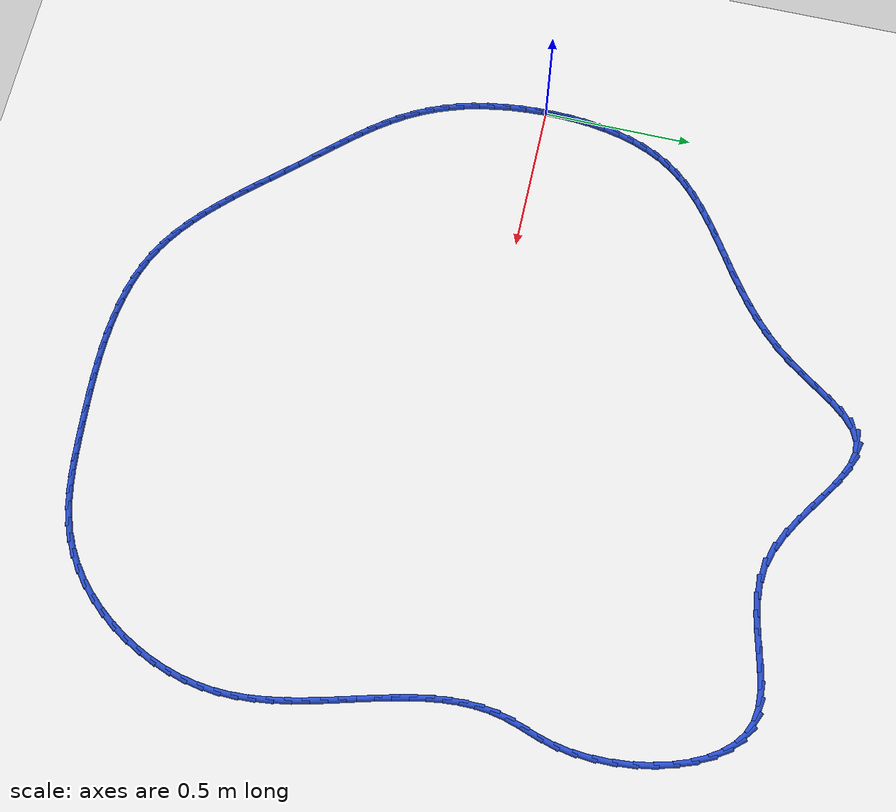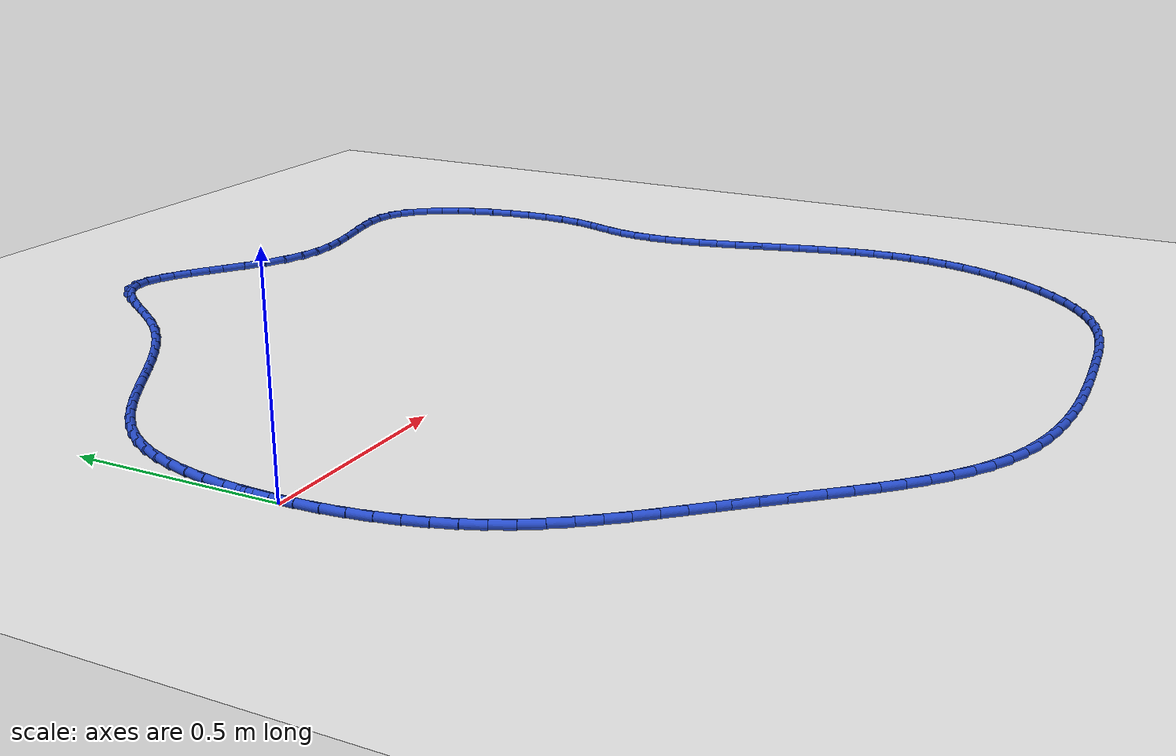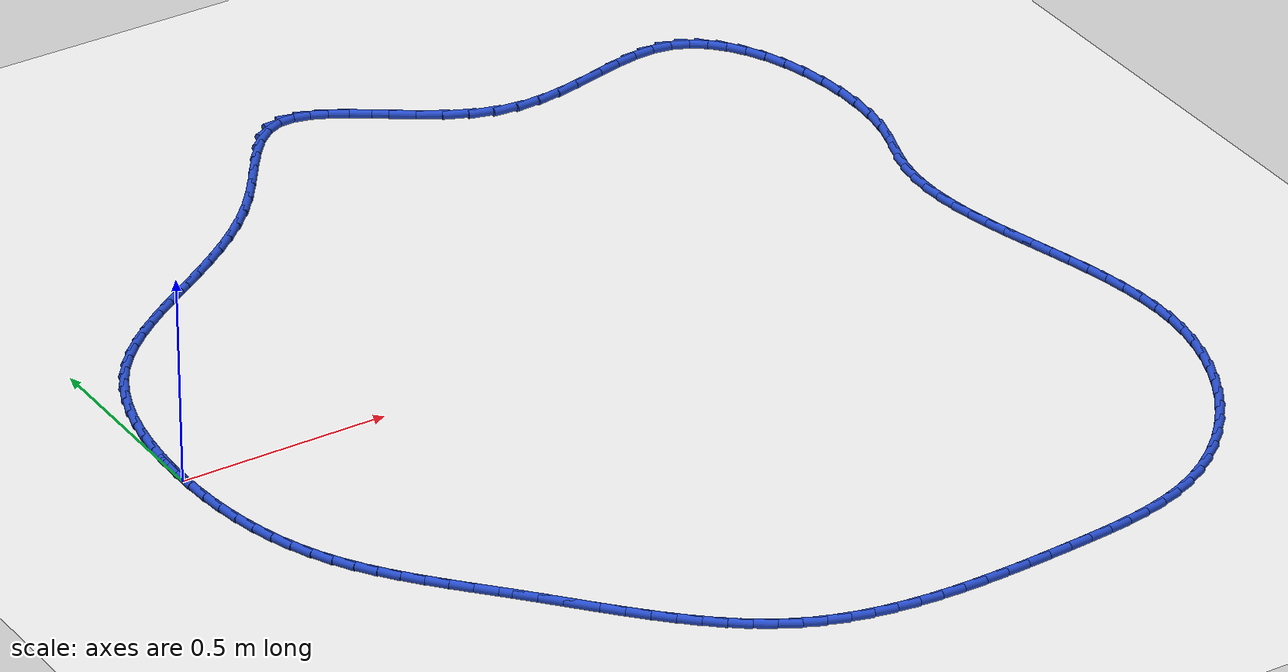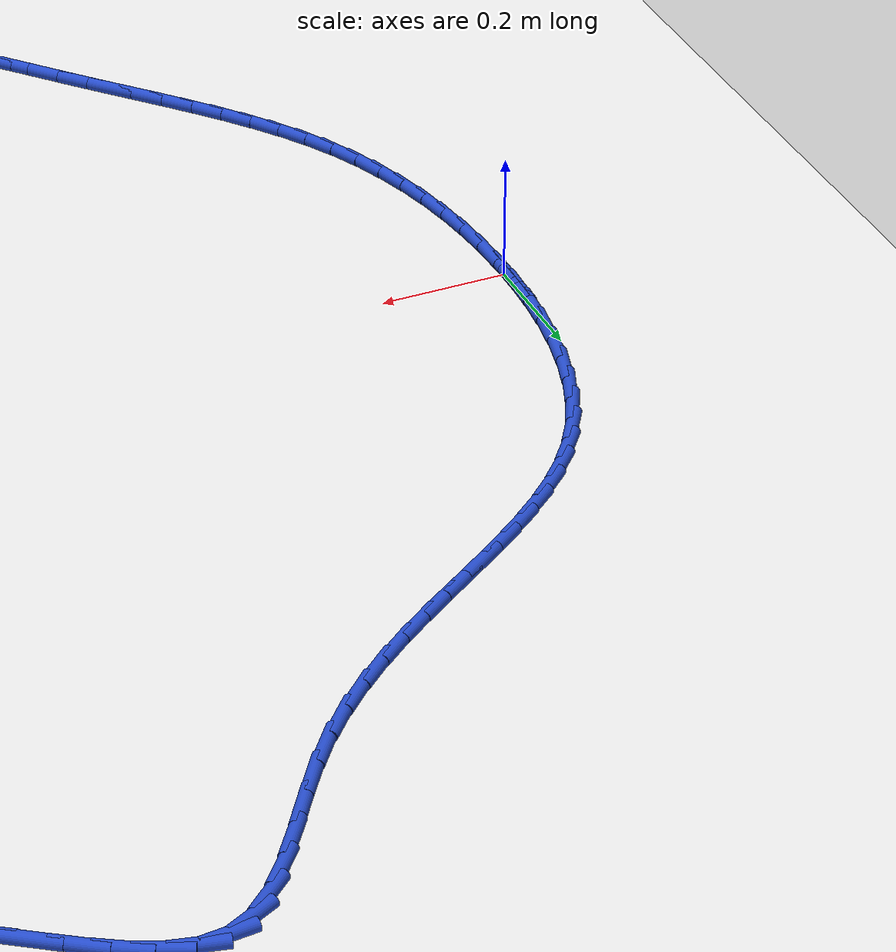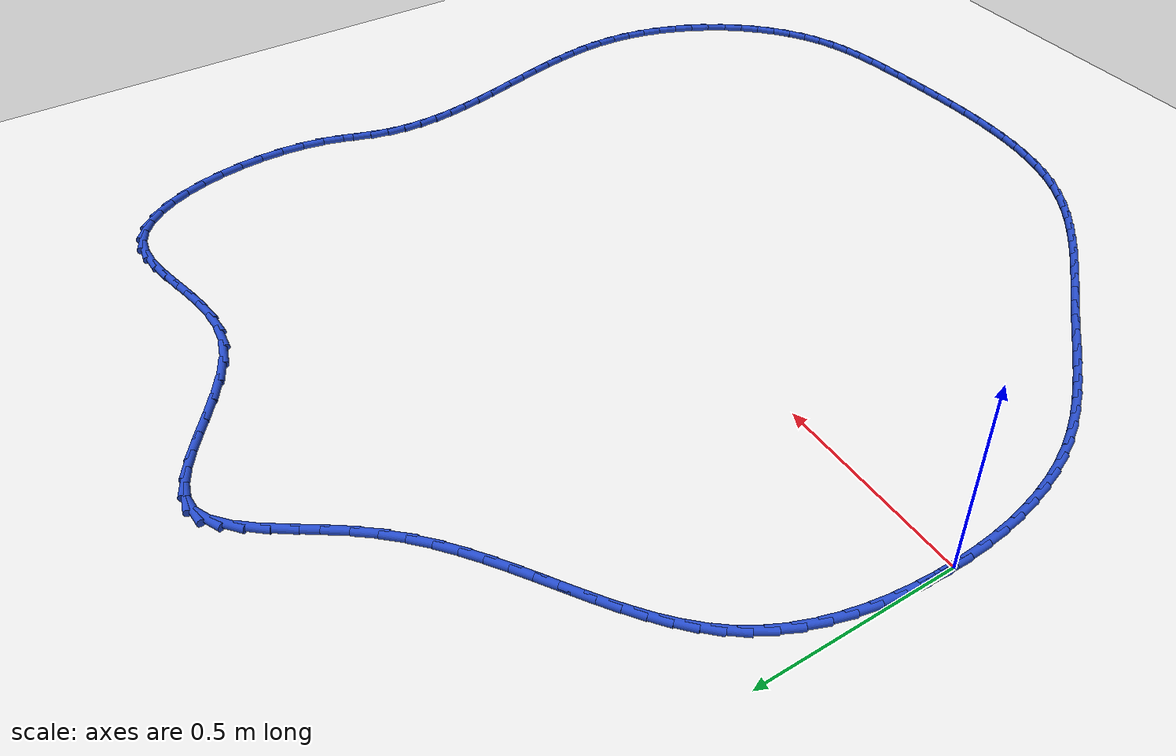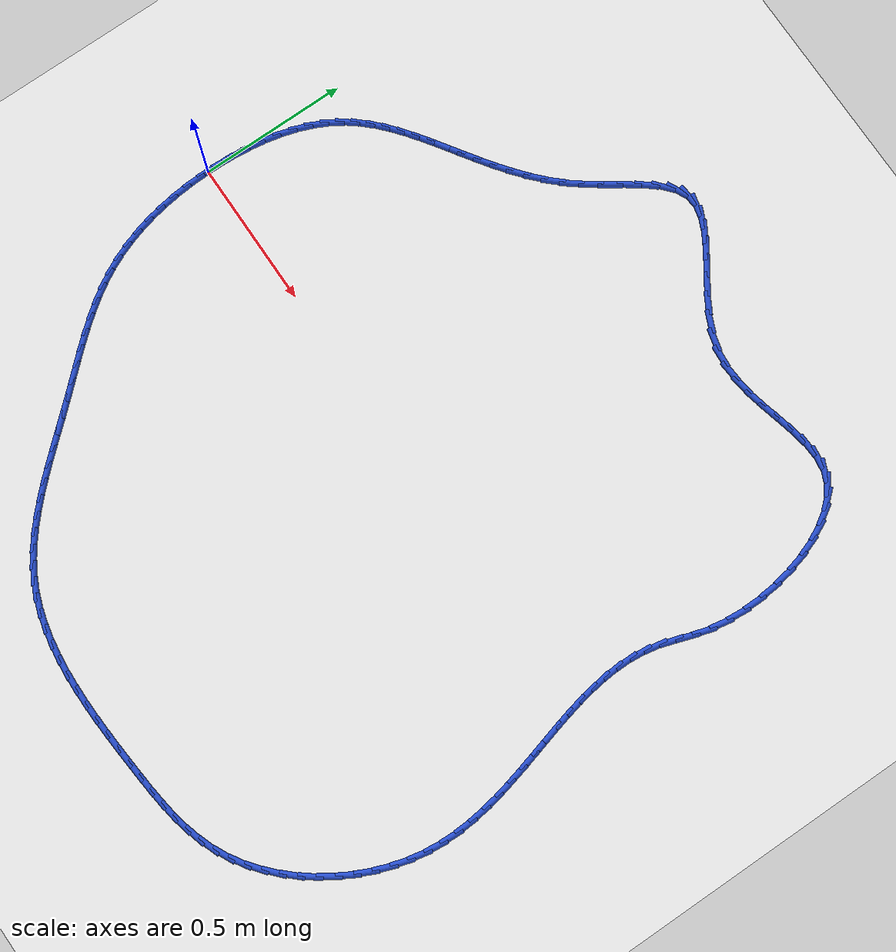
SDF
<sdf version="1.6">
 <world name="default">
  <light name="sun" type="directional">
   <pose>0 0 10 0 -0 0</pose>
   <diffuse>0.8 0.8 0.8 1</diffuse>
   <specular>0.2 0.2 0.2 1</specular>
   <attenuation>
    <range>1000</range>
    <constant>0.9</constant>
    <linear>0.01</linear>
    <quadratic>0.001</quadratic>
   </attenuation>
   <direction>-0.5 0.1 -0.9</direction>
  </light>
  <model name="ground_plane">
   <static>1</static>
   <link name="link">
    <collision name="collision">
     <geometry><plane><normal>0 0 1</normal><size>100 100</size></plane></geometry>
     <surface><friction><ode><mu>100</mu><mu2>50</mu2></ode></friction></surface>
    </collision>
    <visual name="visual">
     <cast_shadows>0</cast_shadows>
     <geometry><plane><normal>0 0 1</normal><size>100 100</size></plane></geometry>
     <material>
      <script><uri>file://media/materials/scripts/gazebo.material</uri><name>Gazebo/WhiteGlow</name></script>
     </material>
    </visual>
   </link>
  </model>
  <gravity>0 0 -9.8</gravity>
  <magnetic_field>6e-06 2.3e-05 -4.2e-05</magnetic_field>
  <atmosphere type="adiabatic"/>
  <physics name="default_physics" default="0" type="ode">
   <max_step_size>0.001</max_step_size>
   <real_time_factor>1</real_time_factor>
   <real_time_update_rate>1000</real_time_update_rate>
  </physics>
  <scene><ambient>0.4 0.4 0.4 1</ambient><background>0.7 0.7 0.7 1</background><shadows>1</shadows></scene>
  <spherical_coordinates>
   <surface_model>EARTH_WGS84</surface_model>
   <latitude_deg>0</latitude_deg>
   <longitude_deg>0</longitude_deg>
   <elevation>0</elevation>
   <heading_deg>0</heading_deg>
  </spherical_coordinates>
  <model name="line">
   <link name="link_0">
    <pose>-6.938893903907228e-18 6.938893903907228e-17 0.01 0 1.57 1.5580120009399903</pose>
    <collision name="collision">
     <geometry><cylinder><radius>0.01</radius><length>0.08</length></cylinder></geometry>
    </collision>
    <visual name="visual">
     <material>
      <script><name>Gazebo/Blue</name><uri>file://media/materials/scripts/gazebo.material</uri></script>
     </material>
     <geometry><cylinder><radius>0.01</radius><length>0.08</length></cylinder></geometry>
    </visual>
   </link>
   <link name="link_1">
    <pose>0.0007160228598828777 0.05600481862712347 0.01 0 1.57 1.5114955153325835</pose>
    <collision name="collision">
     <geometry><cylinder><radius>0.01</radius><length>0.08</length></cylinder></geometry>
    </collision>
    <visual name="visual">
     <material>
      <script><name>Gazebo/Blue</name><uri>file://media/materials/scripts/gazebo.material</uri></script>
     </material>
     <geometry><cylinder><radius>0.01</radius><length>0.08</length></cylinder></geometry>
    </visual>
   </link>
   <link name="link_2">
    <pose>0.00403831065794808 0.11196345447744092 0.01 0 1.57 1.4606617564750028</pose>
    <collision name="collision">
     <geometry><cylinder><radius>0.01</radius><length>0.08</length></cylinder></geometry>
    </collision>
    <visual name="visual">
     <material>
      <script><name>Gazebo/Blue</name><uri>file://media/materials/scripts/gazebo.material</uri></script>
     </material>
     <geometry><cylinder><radius>0.01</radius><length>0.08</length></cylinder></geometry>
    </visual>
   </link>
   <link name="link_3">
    <pose>0.010165736958461995 0.16737413767874326 0.01 0 1.57 1.4043721562110711</pose>
    <collision name="collision">
     <geometry><cylinder><radius>0.01</radius><length>0.08</length></cylinder></geometry>
    </collision>
    <visual name="visual">
     <material>
      <script><name>Gazebo/Blue</name><uri>file://media/materials/scripts/gazebo.material</uri></script>
     </material>
     <geometry><cylinder><radius>0.01</radius><length>0.08</length></cylinder></geometry>
    </visual>
   </link>
   <link name="link_4">
    <pose>0.019297175325691 0.22173509835882108 0.01 0 1.57 1.3413468449461108</pose>
    <collision name="collision">
     <geometry><cylinder><radius>0.01</radius><length>0.08</length></cylinder></geometry>
    </collision>
    <visual name="visual">
     <material>
      <script><name>Gazebo/Blue</name><uri>file://media/materials/scripts/gazebo.material</uri></script>
     </material>
     <geometry><cylinder><radius>0.01</radius><length>0.08</length></cylinder></geometry>
    </visual>
   </link>
   <link name="link_5">
    <pose>0.03163149932390154 0.27454456664546545 0.01 0 1.57 1.2701608311914874</pose>
    <collision name="collision">
     <geometry><cylinder><radius>0.01</radius><length>0.08</length></cylinder></geometry>
    </collision>
    <visual name="visual">
     <material>
      <script><name>Gazebo/Blue</name><uri>file://media/materials/scripts/gazebo.material</uri></script>
     </material>
     <geometry><cylinder><radius>0.01</radius><length>0.08</length></cylinder></geometry>
    </visual>
   </link>
   <link name="link_6">
    <pose>0.04736758251735996 0.32530077266646706 0.01 0 1.57 1.1892843983154922</pose>
    <collision name="collision">
     <geometry><cylinder><radius>0.01</radius><length>0.08</length></cylinder></geometry>
    </collision>
    <visual name="visual">
     <material>
      <script><name>Gazebo/Blue</name><uri>file://media/materials/scripts/gazebo.material</uri></script>
     </material>
     <geometry><cylinder><radius>0.01</radius><length>0.08</length></cylinder></geometry>
    </visual>
   </link>
   <link name="link_7">
    <pose>0.06670429847033266 0.3735019465496166 0.01 0 1.57 1.0972035044235544</pose>
    <collision name="collision">
     <geometry><cylinder><radius>0.01</radius><length>0.08</length></cylinder></geometry>
    </collision>
    <visual name="visual">
     <material>
      <script><name>Gazebo/Blue</name><uri>file://media/materials/scripts/gazebo.material</uri></script>
     </material>
     <geometry><cylinder><radius>0.01</radius><length>0.08</length></cylinder></geometry>
    </visual>
   </link>
   <link name="link_8">
    <pose>0.0898405207470861 0.41864631842270505 0.01 0 1.57 0.9936608406311915</pose>
    <collision name="collision">
     <geometry><cylinder><radius>0.01</radius><length>0.08</length></cylinder></geometry>
    </collision>
    <visual name="visual">
     <material>
      <script><name>Gazebo/Blue</name><uri>file://media/materials/scripts/gazebo.material</uri></script>
     </material>
     <geometry><cylinder><radius>0.01</radius><length>0.08</length></cylinder></geometry>
    </visual>
   </link>
   <link name="link_9">
    <pose>0.11694663111718154 0.460278723929122 0.01 0 1.57 0.8915592658209748</pose>
    <collision name="collision">
     <geometry><cylinder><radius>0.01</radius><length>0.08</length></cylinder></geometry>
    </collision>
    <visual name="visual">
     <material>
      <script><name>Gazebo/Blue</name><uri>file://media/materials/scripts/gazebo.material</uri></script>
     </material>
     <geometry><cylinder><radius>0.01</radius><length>0.08</length></cylinder></geometry>
    </visual>
   </link>
   <link name="link_10">
    <pose>0.14783302362325507 0.4985328494251099 0.01 0 1.57 0.8023782002441536</pose>
    <collision name="collision">
     <geometry><cylinder><radius>0.01</radius><length>0.08</length></cylinder></geometry>
    </collision>
    <visual name="visual">
     <material>
      <script><name>Gazebo/Blue</name><uri>file://media/materials/scripts/gazebo.material</uri></script>
     </material>
     <geometry><cylinder><radius>0.01</radius><length>0.08</length></cylinder></geometry>
    </visual>
   </link>
   <link name="link_11">
    <pose>0.18206340806843252 0.5339458955520405 0.01 0 1.57 0.7282899464413584</pose>
    <collision name="collision">
     <geometry><cylinder><radius>0.01</radius><length>0.08</length></cylinder></geometry>
    </collision>
    <visual name="visual">
     <material>
      <script><name>Gazebo/Blue</name><uri>file://media/materials/scripts/gazebo.material</uri></script>
     </material>
     <geometry><cylinder><radius>0.01</radius><length>0.08</length></cylinder></geometry>
    </visual>
   </link>
   <link name="link_12">
    <pose>0.21919668286336333 0.5670629331970674 0.01 0 1.57 0.6699495018898777</pose>
    <collision name="collision">
     <geometry><cylinder><radius>0.01</radius><length>0.08</length></cylinder></geometry>
    </collision>
    <visual name="visual">
     <material>
      <script><name>Gazebo/Blue</name><uri>file://media/materials/scripts/gazebo.material</uri></script>
     </material>
     <geometry><cylinder><radius>0.01</radius><length>0.08</length></cylinder></geometry>
    </visual>
   </link>
   <link name="link_13">
    <pose>0.25879174641869707 0.5984290332473446 0.01 0 1.57 0.6271319856668433</pose>
    <collision name="collision">
     <geometry><cylinder><radius>0.01</radius><length>0.08</length></cylinder></geometry>
    </collision>
    <visual name="visual">
     <material>
      <script><name>Gazebo/Blue</name><uri>file://media/materials/scripts/gazebo.material</uri></script>
     </material>
     <geometry><cylinder><radius>0.01</radius><length>0.08</length></cylinder></geometry>
    </visual>
   </link>
   <link name="link_14">
    <pose>0.30040749714508286 0.6285892665900253 0.01 0 1.57 0.5991782193303513</pose>
    <collision name="collision">
     <geometry><cylinder><radius>0.01</radius><length>0.08</length></cylinder></geometry>
    </collision>
    <visual name="visual">
     <material>
      <script><name>Gazebo/Blue</name><uri>file://media/materials/scripts/gazebo.material</uri></script>
     </material>
     <geometry><cylinder><radius>0.01</radius><length>0.08</length></cylinder></geometry>
    </visual>
   </link>
   <link name="link_15">
    <pose>0.34360283345317055 0.6580887041122638 0.01 0 1.57 0.5853092490850328</pose>
    <collision name="collision">
     <geometry><cylinder><radius>0.01</radius><length>0.08</length></cylinder></geometry>
    </collision>
    <visual name="visual">
     <material>
      <script><name>Gazebo/Blue</name><uri>file://media/materials/scripts/gazebo.material</uri></script>
     </material>
     <geometry><cylinder><radius>0.01</radius><length>0.08</length></cylinder></geometry>
    </visual>
   </link>
   <link name="link_16">
    <pose>0.3879366537536095 0.6874724167012136 0.01 0 1.57 0.5848019640146941</pose>
    <collision name="collision">
     <geometry><cylinder><radius>0.01</radius><length>0.08</length></cylinder></geometry>
    </collision>
    <visual name="visual">
     <material>
      <script><name>Gazebo/Blue</name><uri>file://media/materials/scripts/gazebo.material</uri></script>
     </material>
     <geometry><cylinder><radius>0.01</radius><length>0.08</length></cylinder></geometry>
    </visual>
   </link>
   <link name="link_17">
    <pose>0.4329678564570491 0.7172854752440283 0.01 0 1.57 0.5970556516180642</pose>
    <collision name="collision">
     <geometry><cylinder><radius>0.01</radius><length>0.08</length></cylinder></geometry>
    </collision>
    <visual name="visual">
     <material>
      <script><name>Gazebo/Blue</name><uri>file://media/materials/scripts/gazebo.material</uri></script>
     </material>
     <geometry><cylinder><radius>0.01</radius><length>0.08</length></cylinder></geometry>
    </visual>
   </link>
   <link name="link_18">
    <pose>0.47825533997413866 0.7480729506278618 0.01 0 1.57 0.6215809120737144</pose>
    <collision name="collision">
     <geometry><cylinder><radius>0.01</radius><length>0.08</length></cylinder></geometry>
    </collision>
    <visual name="visual">
     <material>
      <script><name>Gazebo/Blue</name><uri>file://media/materials/scripts/gazebo.material</uri></script>
     </material>
     <geometry><cylinder><radius>0.01</radius><length>0.08</length></cylinder></geometry>
    </visual>
   </link>
   <link name="link_19">
    <pose>0.5233580027155281 0.780379913739868 0.01 0 1.57 0.6579326872274103</pose>
    <collision name="collision">
     <geometry><cylinder><radius>0.01</radius><length>0.08</length></cylinder></geometry>
    </collision>
    <visual name="visual">
     <material>
      <script><name>Gazebo/Blue</name><uri>file://media/materials/scripts/gazebo.material</uri></script>
     </material>
     <geometry><cylinder><radius>0.01</radius><length>0.08</length></cylinder></geometry>
    </visual>
   </link>
   <link name="link_20">
    <pose>0.5678347430918664 0.8147514354672004 0.01 0 1.57 0.7056016022560662</pose>
    <collision name="collision">
     <geometry><cylinder><radius>0.01</radius><length>0.08</length></cylinder></geometry>
    </collision>
    <visual name="visual">
     <material>
      <script><name>Gazebo/Blue</name><uri>file://media/materials/scripts/gazebo.material</uri></script>
     </material>
     <geometry><cylinder><radius>0.01</radius><length>0.08</length></cylinder></geometry>
    </visual>
   </link>
   <link name="link_21">
    <pose>0.6112444595138036 0.8517325866970131 0.01 0 1.57 0.7638779085880193</pose>
    <collision name="collision">
     <geometry><cylinder><radius>0.01</radius><length>0.08</length></cylinder></geometry>
    </collision>
    <visual name="visual">
     <material>
      <script><name>Gazebo/Blue</name><uri>file://media/materials/scripts/gazebo.material</uri></script>
     </material>
     <geometry><cylinder><radius>0.01</radius><length>0.08</length></cylinder></geometry>
    </visual>
   </link>
   <link name="link_22">
    <pose>0.6531460503919884 0.8918684383164589 0.01 0 1.57 0.8317112746587209</pose>
    <collision name="collision">
     <geometry><cylinder><radius>0.01</radius><length>0.08</length></cylinder></geometry>
    </collision>
    <visual name="visual">
     <material>
      <script><name>Gazebo/Blue</name><uri>file://media/materials/scripts/gazebo.material</uri></script>
     </material>
     <geometry><cylinder><radius>0.01</radius><length>0.08</length></cylinder></geometry>
    </visual>
   </link>
   <link name="link_23">
    <pose>0.6930984141370711 0.9357040612126928 0.01 0 1.57 0.9054417929205705</pose>
    <collision name="collision">
     <geometry><cylinder><radius>0.01</radius><length>0.08</length></cylinder></geometry>
    </collision>
    <visual name="visual">
     <material>
      <script><name>Gazebo/Blue</name><uri>file://media/materials/scripts/gazebo.material</uri></script>
     </material>
     <geometry><cylinder><radius>0.01</radius><length>0.08</length></cylinder></geometry>
    </visual>
   </link>
   <link name="link_24">
    <pose>0.7307111971477394 0.9836354958245229 0.01 0 1.57 0.956693167705404</pose>
    <collision name="collision">
     <geometry><cylinder><radius>0.01</radius><length>0.08</length></cylinder></geometry>
    </collision>
    <visual name="visual">
     <material>
      <script><name>Gazebo/Blue</name><uri>file://media/materials/scripts/gazebo.material</uri></script>
     </material>
     <geometry><cylinder><radius>0.01</radius><length>0.08</length></cylinder></geometry>
    </visual>
   </link>
   <link name="link_25">
    <pose>0.7662707702710859 1.0340714614801394 0.01 0 1.57 0.9692664904671359</pose>
    <collision name="collision">
     <geometry><cylinder><radius>0.01</radius><length>0.08</length></cylinder></geometry>
    </collision>
    <visual name="visual">
     <material>
      <script><name>Gazebo/Blue</name><uri>file://media/materials/scripts/gazebo.material</uri></script>
     </material>
     <geometry><cylinder><radius>0.01</radius><length>0.08</length></cylinder></geometry>
    </visual>
   </link>
   <link name="link_26">
    <pose>0.8005451846684318 1.0840061380163684 0.01 0 1.57 0.9416594743193045</pose>
    <collision name="collision">
     <geometry><cylinder><radius>0.01</radius><length>0.08</length></cylinder></geometry>
    </collision>
    <visual name="visual">
     <material>
      <script><name>Gazebo/Blue</name><uri>file://media/materials/scripts/gazebo.material</uri></script>
     </material>
     <geometry><cylinder><radius>0.01</radius><length>0.08</length></cylinder></geometry>
    </visual>
   </link>
   <link name="link_27">
    <pose>0.8343128116850024 1.1304033982235218 0.01 0 1.57 0.8635527067257923</pose>
    <collision name="collision">
     <geometry><cylinder><radius>0.01</radius><length>0.08</length></cylinder></geometry>
    </collision>
    <visual name="visual">
     <material>
      <script><name>Gazebo/Blue</name><uri>file://media/materials/scripts/gazebo.material</uri></script>
     </material>
     <geometry><cylinder><radius>0.01</radius><length>0.08</length></cylinder></geometry>
    </visual>
   </link>
   <link name="link_28">
    <pose>0.8683520226660215 1.1702271148919097 0.01 0 1.57 0.7108827795449572</pose>
    <collision name="collision">
     <geometry><cylinder><radius>0.01</radius><length>0.08</length></cylinder></geometry>
    </collision>
    <visual name="visual">
     <material>
      <script><name>Gazebo/Blue</name><uri>file://media/materials/scripts/gazebo.material</uri></script>
     </material>
     <geometry><cylinder><radius>0.01</radius><length>0.08</length></cylinder></geometry>
    </visual>
   </link>
   <link name="link_29">
    <pose>0.9034411889567143 1.200441160811844 0.01 0 1.57 0.44416503624874554</pose>
    <collision name="collision">
     <geometry><cylinder><radius>0.01</radius><length>0.08</length></cylinder></geometry>
    </collision>
    <visual name="visual">
     <material>
      <script><name>Gazebo/Blue</name><uri>file://media/materials/scripts/gazebo.material</uri></script>
     </material>
     <geometry><cylinder><radius>0.01</radius><length>0.08</length></cylinder></geometry>
    </visual>
   </link>
   <link name="link_30">
    <pose>0.9403586817886175 1.2180094094747382 0.01 0 1.57 0.07290509189926322</pose>
    <collision name="collision">
     <geometry><cylinder><radius>0.01</radius><length>0.08</length></cylinder></geometry>
    </collision>
    <visual name="visual">
     <material>
      <script><name>Gazebo/Blue</name><uri>file://media/materials/scripts/gazebo.material</uri></script>
     </material>
     <geometry><cylinder><radius>0.01</radius><length>0.08</length></cylinder></geometry>
    </visual>
   </link>
   <link name="link_31">
    <pose>0.9797225660596379 1.2208843324320524 0.01 0 1.57 -0.23517942414482865</pose>
    <collision name="collision">
     <geometry><cylinder><radius>0.01</radius><length>0.08</length></cylinder></geometry>
    </collision>
    <visual name="visual">
     <material>
      <script><name>Gazebo/Blue</name><uri>file://media/materials/scripts/gazebo.material</uri></script>
     </material>
     <geometry><cylinder><radius>0.01</radius><length>0.08</length></cylinder></geometry>
    </visual>
   </link>
   <link name="link_32">
    <pose>1.0215267573041287 1.2108674871447895 0.01 0 1.57 -0.4290888746792979</pose>
    <collision name="collision">
     <geometry><cylinder><radius>0.01</radius><length>0.08</length></cylinder></geometry>
    </collision>
    <visual name="visual">
     <material>
      <script><name>Gazebo/Blue</name><uri>file://media/materials/scripts/gazebo.material</uri></script>
     </material>
     <geometry><cylinder><radius>0.01</radius><length>0.08</length></cylinder></geometry>
    </visual>
   </link>
   <link name="link_33">
    <pose>1.06561328962018 1.1906970733752646 0.01 0 1.57 -0.5381767272477964</pose>
    <collision name="collision">
     <geometry><cylinder><radius>0.01</radius><length>0.08</length></cylinder></geometry>
    </collision>
    <visual name="visual">
     <material>
      <script><name>Gazebo/Blue</name><uri>file://media/materials/scripts/gazebo.material</uri></script>
     </material>
     <geometry><cylinder><radius>0.01</radius><length>0.08</length></cylinder></geometry>
    </visual>
   </link>
   <link name="link_34">
    <pose>1.1118241971058818 1.1631112908857915 0.01 0 1.57 -0.5900796372655672</pose>
    <collision name="collision">
     <geometry><cylinder><radius>0.01</radius><length>0.08</length></cylinder></geometry>
    </collision>
    <visual name="visual">
     <material>
      <script><name>Gazebo/Blue</name><uri>file://media/materials/scripts/gazebo.material</uri></script>
     </material>
     <geometry><cylinder><radius>0.01</radius><length>0.08</length></cylinder></geometry>
    </visual>
   </link>
   <link name="link_35">
    <pose>1.1600015138593243 1.130848339438685 0.01 0 1.57 -0.6000657120836914</pose>
    <collision name="collision">
     <geometry><cylinder><radius>0.01</radius><length>0.08</length></cylinder></geometry>
    </collision>
    <visual name="visual">
     <material>
      <script><name>Gazebo/Blue</name><uri>file://media/materials/scripts/gazebo.material</uri></script>
     </material>
     <geometry><cylinder><radius>0.01</radius><length>0.08</length></cylinder></geometry>
    </visual>
   </link>
   <link name="link_36">
    <pose>1.2099872739785975 1.0966464187962601 0.01 0 1.57 -0.5741820575036555</pose>
    <collision name="collision">
     <geometry><cylinder><radius>0.01</radius><length>0.08</length></cylinder></geometry>
    </collision>
    <visual name="visual">
     <material>
      <script><name>Gazebo/Blue</name><uri>file://media/materials/scripts/gazebo.material</uri></script>
     </material>
     <geometry><cylinder><radius>0.01</radius><length>0.08</length></cylinder></geometry>
    </visual>
   </link>
   <link name="link_37">
    <pose>1.2616235115617924 1.0632437287208305 0.01 0 1.57 -0.5121082902583999</pose>
    <collision name="collision">
     <geometry><cylinder><radius>0.01</radius><length>0.08</length></cylinder></geometry>
    </collision>
    <visual name="visual">
     <material>
      <script><name>Gazebo/Blue</name><uri>file://media/materials/scripts/gazebo.material</uri></script>
     </material>
     <geometry><cylinder><radius>0.01</radius><length>0.08</length></cylinder></geometry>
    </visual>
   </link>
   <link name="link_38">
    <pose>1.3147522607069984 1.0333784689747114 0.01 0 1.57 -0.408735743502697</pose>
    <collision name="collision">
     <geometry><cylinder><radius>0.01</radius><length>0.08</length></cylinder></geometry>
    </collision>
    <visual name="visual">
     <material>
      <script><name>Gazebo/Blue</name><uri>file://media/materials/scripts/gazebo.material</uri></script>
     </material>
     <geometry><cylinder><radius>0.01</radius><length>0.08</length></cylinder></geometry>
    </visual>
   </link>
   <link name="link_39">
    <pose>1.3692155555123058 1.0097888393202168 0.01 0 1.57 -0.25638457633578776</pose>
    <collision name="collision">
     <geometry><cylinder><radius>0.01</radius><length>0.08</length></cylinder></geometry>
    </collision>
    <visual name="visual">
     <material>
      <script><name>Gazebo/Blue</name><uri>file://media/materials/scripts/gazebo.material</uri></script>
     </material>
     <geometry><cylinder><radius>0.01</radius><length>0.08</length></cylinder></geometry>
    </visual>
   </link>
   <link name="link_40">
    <pose>1.4248546900250234 0.9952028195085528 0.01 0 1.57 -0.07777250917921845</pose>
    <collision name="collision">
     <geometry><cylinder><radius>0.01</radius><length>0.08</length></cylinder></geometry>
    </collision>
    <visual name="visual">
     <material>
      <script><name>Gazebo/Blue</name><uri>file://media/materials/scripts/gazebo.material</uri></script>
     </material>
     <geometry><cylinder><radius>0.01</radius><length>0.08</length></cylinder></geometry>
    </visual>
   </link>
   <link name="link_41">
    <pose>1.4813985737160171 0.9907963719852275 0.01 0 1.57 0.06572686670619221</pose>
    <collision name="collision">
     <geometry><cylinder><radius>0.01</radius><length>0.08</length></cylinder></geometry>
    </collision>
    <visual name="visual">
     <material>
      <script><name>Gazebo/Blue</name><uri>file://media/materials/scripts/gazebo.material</uri></script>
     </material>
     <geometry><cylinder><radius>0.01</radius><length>0.08</length></cylinder></geometry>
    </visual>
   </link>
   <link name="link_42">
    <pose>1.538344338381511 0.9945446377529665 0.01 0 1.57 0.1653808120447469</pose>
    <collision name="collision">
     <geometry><cylinder><radius>0.01</radius><length>0.08</length></cylinder></geometry>
    </collision>
    <visual name="visual">
     <material>
      <script><name>Gazebo/Blue</name><uri>file://media/materials/scripts/gazebo.material</uri></script>
     </material>
     <geometry><cylinder><radius>0.01</radius><length>0.08</length></cylinder></geometry>
    </visual>
   </link>
   <link name="link_43">
    <pose>1.5951604983177008 1.0040275536263747 0.01 0 1.57 0.2240689625554522</pose>
    <collision name="collision">
     <geometry><cylinder><radius>0.01</radius><length>0.08</length></cylinder></geometry>
    </collision>
    <visual name="visual">
     <material>
      <script><name>Gazebo/Blue</name><uri>file://media/materials/scripts/gazebo.material</uri></script>
     </material>
     <geometry><cylinder><radius>0.01</radius><length>0.08</length></cylinder></geometry>
    </visual>
   </link>
   <link name="link_44">
    <pose>1.6513155678207823 1.0168250564200558 0.01 0 1.57 0.24414631944973658</pose>
    <collision name="collision">
     <geometry><cylinder><radius>0.01</radius><length>0.08</length></cylinder></geometry>
    </collision>
    <visual name="visual">
     <material>
      <script><name>Gazebo/Blue</name><uri>file://media/materials/scripts/gazebo.material</uri></script>
     </material>
     <geometry><cylinder><radius>0.01</radius><length>0.08</length></cylinder></geometry>
    </visual>
   </link>
   <link name="link_45">
    <pose>1.7062780611869508 1.0305170829486159 0.01 0 1.57 0.22467015988949632</pose>
    <collision name="collision">
     <geometry><cylinder><radius>0.01</radius><length>0.08</length></cylinder></geometry>
    </collision>
    <visual name="visual">
     <material>
      <script><name>Gazebo/Blue</name><uri>file://media/materials/scripts/gazebo.material</uri></script>
     </material>
     <geometry><cylinder><radius>0.01</radius><length>0.08</length></cylinder></geometry>
    </visual>
   </link>
   <link name="link_46">
    <pose>1.7595164927124025 1.042683570026659 0.01 0 1.57 0.15987180391792022</pose>
    <collision name="collision">
     <geometry><cylinder><radius>0.01</radius><length>0.08</length></cylinder></geometry>
    </collision>
    <visual name="visual">
     <material>
      <script><name>Gazebo/Blue</name><uri>file://media/materials/scripts/gazebo.material</uri></script>
     </material>
     <geometry><cylinder><radius>0.01</radius><length>0.08</length></cylinder></geometry>
    </visual>
   </link>
   <link name="link_47">
    <pose>1.8104993766933322 1.0509044544687896 0.01 0 1.57 0.038474331121059906</pose>
    <collision name="collision">
     <geometry><cylinder><radius>0.01</radius><length>0.08</length></cylinder></geometry>
    </collision>
    <visual name="visual">
     <material>
      <script><name>Gazebo/Blue</name><uri>file://media/materials/scripts/gazebo.material</uri></script>
     </material>
     <geometry><cylinder><radius>0.01</radius><length>0.08</length></cylinder></geometry>
    </visual>
   </link>
   <link name="link_48">
    <pose>1.8586952274259363 1.0527596730896125 0.01 0 1.57 -0.1532218894098518</pose>
    <collision name="collision">
     <geometry><cylinder><radius>0.01</radius><length>0.08</length></cylinder></geometry>
    </collision>
    <visual name="visual">
     <material>
      <script><name>Gazebo/Blue</name><uri>file://media/materials/scripts/gazebo.material</uri></script>
     </material>
     <geometry><cylinder><radius>0.01</radius><length>0.08</length></cylinder></geometry>
    </visual>
   </link>
   <link name="link_49">
    <pose>1.9035725592064092 1.0458291627037324 0.01 0 1.57 -0.4091834556531191</pose>
    <collision name="collision">
     <geometry><cylinder><radius>0.01</radius><length>0.08</length></cylinder></geometry>
    </collision>
    <visual name="visual">
     <material>
      <script><name>Gazebo/Blue</name><uri>file://media/materials/scripts/gazebo.material</uri></script>
     </material>
     <geometry><cylinder><radius>0.01</radius><length>0.08</length></cylinder></geometry>
    </visual>
   </link>
   <link name="link_50">
    <pose>1.9446341344281903 1.0280223689619927 0.01 0 1.57 -0.653995918955852</pose>
    <collision name="collision">
     <geometry><cylinder><radius>0.01</radius><length>0.08</length></cylinder></geometry>
    </collision>
    <visual name="visual">
     <material>
      <script><name>Gazebo/Blue</name><uri>file://media/materials/scripts/gazebo.material</uri></script>
     </material>
     <geometry><cylinder><radius>0.01</radius><length>0.08</length></cylinder></geometry>
    </visual>
   </link>
   <link name="link_51">
    <pose>1.981633470615388 0.9996613104154259 0.01 0 1.57 -0.8523984370859096</pose>
    <collision name="collision">
     <geometry><cylinder><radius>0.01</radius><length>0.08</length></cylinder></geometry>
    </collision>
    <visual name="visual">
     <material>
      <script><name>Gazebo/Blue</name><uri>file://media/materials/scripts/gazebo.material</uri></script>
     </material>
     <geometry><cylinder><radius>0.01</radius><length>0.08</length></cylinder></geometry>
    </visual>
   </link>
   <link name="link_52">
    <pose>2.014435557715865 0.9621405074934283 0.01 0 1.57 -1.0095079521292303</pose>
    <collision name="collision">
     <geometry><cylinder><radius>0.01</radius><length>0.08</length></cylinder></geometry>
    </collision>
    <visual name="visual">
     <material>
      <script><name>Gazebo/Blue</name><uri>file://media/materials/scripts/gazebo.material</uri></script>
     </material>
     <geometry><cylinder><radius>0.01</radius><length>0.08</length></cylinder></geometry>
    </visual>
   </link>
   <link name="link_53">
    <pose>2.04290589214038 0.9168593534216699 0.01 0 1.57 -1.1356899805627934</pose>
    <collision name="collision">
     <geometry><cylinder><radius>0.01</radius><length>0.08</length></cylinder></geometry>
    </collision>
    <visual name="visual">
     <material>
      <script><name>Gazebo/Blue</name><uri>file://media/materials/scripts/gazebo.material</uri></script>
     </material>
     <geometry><cylinder><radius>0.01</radius><length>0.08</length></cylinder></geometry>
    </visual>
   </link>
   <link name="link_54">
    <pose>2.066909970299694 0.8652172414258206 0.01 0 1.57 -1.2405567775127413</pose>
    <collision name="collision">
     <geometry><cylinder><radius>0.01</radius><length>0.08</length></cylinder></geometry>
    </collision>
    <visual name="visual">
     <material>
      <script><name>Gazebo/Blue</name><uri>file://media/materials/scripts/gazebo.material</uri></script>
     </material>
     <geometry><cylinder><radius>0.01</radius><length>0.08</length></cylinder></geometry>
    </visual>
   </link>
   <link name="link_55">
    <pose>2.0863132886045648 0.8086135647315492 0.01 0 1.57 -1.3316673609923124</pose>
    <collision name="collision">
     <geometry><cylinder><radius>0.01</radius><length>0.08</length></cylinder></geometry>
    </collision>
    <visual name="visual">
     <material>
      <script><name>Gazebo/Blue</name><uri>file://media/materials/scripts/gazebo.material</uri></script>
     </material>
     <geometry><cylinder><radius>0.01</radius><length>0.08</length></cylinder></geometry>
    </visual>
   </link>
   <link name="link_56">
    <pose>2.100981343465755 0.7484477165645266 0.01 0 1.57 -1.4148687941108253</pose>
    <collision name="collision">
     <geometry><cylinder><radius>0.01</radius><length>0.08</length></cylinder></geometry>
    </collision>
    <visual name="visual">
     <material>
      <script><name>Gazebo/Blue</name><uri>file://media/materials/scripts/gazebo.material</uri></script>
     </material>
     <geometry><cylinder><radius>0.01</radius><length>0.08</length></cylinder></geometry>
    </visual>
   </link>
   <link name="link_57">
    <pose>2.1107796312940224 0.6861190901504215 0.01 0 1.57 -1.4949575224449192</pose>
    <collision name="collision">
     <geometry><cylinder><radius>0.01</radius><length>0.08</length></cylinder></geometry>
    </collision>
    <visual name="visual">
     <material>
      <script><name>Gazebo/Blue</name><uri>file://media/materials/scripts/gazebo.material</uri></script>
     </material>
     <geometry><cylinder><radius>0.01</radius><length>0.08</length></cylinder></geometry>
    </visual>
   </link>
   <link name="link_58">
    <pose>2.115573648500128 0.6230270787149047 0.01 0 1.57 1.565276384981466</pose>
    <collision name="collision">
     <geometry><cylinder><radius>0.01</radius><length>0.08</length></cylinder></geometry>
    </collision>
    <visual name="visual">
     <material>
      <script><name>Gazebo/Blue</name><uri>file://media/materials/scripts/gazebo.material</uri></script>
     </material>
     <geometry><cylinder><radius>0.01</radius><length>0.08</length></cylinder></geometry>
    </visual>
   </link>
   <link name="link_59">
    <pose>2.115228891494831 0.5605710754836447 0.01 0 1.57 1.4780808034710937</pose>
    <collision name="collision">
     <geometry><cylinder><radius>0.01</radius><length>0.08</length></cylinder></geometry>
    </collision>
    <visual name="visual">
     <material>
      <script><name>Gazebo/Blue</name><uri>file://media/materials/scripts/gazebo.material</uri></script>
     </material>
     <geometry><cylinder><radius>0.01</radius><length>0.08</length></cylinder></geometry>
    </visual>
   </link>
   <link name="link_60">
    <pose>2.1096108566888923 0.5001504736823129 0.01 0 1.57 1.379675724442057</pose>
    <collision name="collision">
     <geometry><cylinder><radius>0.01</radius><length>0.08</length></cylinder></geometry>
    </collision>
    <visual name="visual">
     <material>
      <script><name>Gazebo/Blue</name><uri>file://media/materials/scripts/gazebo.material</uri></script>
     </material>
     <geometry><cylinder><radius>0.01</radius><length>0.08</length></cylinder></geometry>
    </visual>
   </link>
   <link name="link_61">
    <pose>2.0985851101695077 0.4431646112976795 0.01 0 1.57 1.280404094229952</pose>
    <collision name="collision">
     <geometry><cylinder><radius>0.01</radius><length>0.08</length></cylinder></geometry>
    </collision>
    <visual name="visual">
     <material>
      <script><name>Gazebo/Blue</name><uri>file://media/materials/scripts/gazebo.material</uri></script>
     </material>
     <geometry><cylinder><radius>0.01</radius><length>0.08</length></cylinder></geometry>
    </visual>
   </link>
   <link name="link_62">
    <pose>2.082811816340875 0.3903828753914755 0.01 0 1.57 1.2413578714222</pose>
    <collision name="collision">
     <geometry><cylinder><radius>0.01</radius><length>0.08</length></cylinder></geometry>
    </collision>
    <visual name="visual">
     <material>
      <script><name>Gazebo/Blue</name><uri>file://media/materials/scripts/gazebo.material</uri></script>
     </material>
     <geometry><cylinder><radius>0.01</radius><length>0.08</length></cylinder></geometry>
    </visual>
   </link>
   <link name="link_63">
    <pose>2.0657166895979553 0.3403821480356148 0.01 0 1.57 1.2856585230784037</pose>
    <collision name="collision">
     <geometry><cylinder><radius>0.01</radius><length>0.08</length></cylinder></geometry>
    </collision>
    <visual name="visual">
     <material>
      <script><name>Gazebo/Blue</name><uri>file://media/materials/scripts/gazebo.material</uri></script>
     </material>
     <geometry><cylinder><radius>0.01</radius><length>0.08</length></cylinder></geometry>
    </visual>
   </link>
   <link name="link_64">
    <pose>2.0513194067636875 0.2912656584978353 0.01 0 1.57 1.3906167535318301</pose>
    <collision name="collision">
     <geometry><cylinder><radius>0.01</radius><length>0.08</length></cylinder></geometry>
    </collision>
    <visual name="visual">
     <material>
      <script><name>Gazebo/Blue</name><uri>file://media/materials/scripts/gazebo.material</uri></script>
     </material>
     <geometry><cylinder><radius>0.01</radius><length>0.08</length></cylinder></geometry>
    </visual>
   </link>
   <link name="link_65">
    <pose>2.042290206699731 0.24169689914759868 0.01 0 1.57 1.4930259900293474</pose>
    <collision name="collision">
     <geometry><cylinder><radius>0.01</radius><length>0.08</length></cylinder></geometry>
    </collision>
    <visual name="visual">
     <material>
      <script><name>Gazebo/Blue</name><uri>file://media/materials/scripts/gazebo.material</uri></script>
     </material>
     <geometry><cylinder><radius>0.01</radius><length>0.08</length></cylinder></geometry>
    </visual>
   </link>
   <link name="link_66">
    <pose>2.0383824160397963 0.1915504134283528 0.01 0 1.57 -1.5592285374577033</pose>
    <collision name="collision">
     <geometry><cylinder><radius>0.01</radius><length>0.08</length></cylinder></geometry>
    </collision>
    <visual name="visual">
     <material>
      <script><name>Gazebo/Blue</name><uri>file://media/materials/scripts/gazebo.material</uri></script>
     </material>
     <geometry><cylinder><radius>0.01</radius><length>0.08</length></cylinder></geometry>
    </visual>
   </link>
   <link name="link_67">
    <pose>2.0389688328703297 0.14085873359837492 0.01 0 1.57 -1.4840411063616188</pose>
    <collision name="collision">
     <geometry><cylinder><radius>0.01</radius><length>0.08</length></cylinder></geometry>
    </collision>
    <visual name="visual">
     <material>
      <script><name>Gazebo/Blue</name><uri>file://media/materials/scripts/gazebo.material</uri></script>
     </material>
     <geometry><cylinder><radius>0.01</radius><length>0.08</length></cylinder></geometry>
    </visual>
   </link>
   <link name="link_68">
    <pose>2.043422255277775 0.08965439191594038 0.01 0 1.57 -1.4230314044231713</pose>
    <collision name="collision">
     <geometry><cylinder><radius>0.01</radius><length>0.08</length></cylinder></geometry>
    </collision>
    <visual name="visual">
     <material>
      <script><name>Gazebo/Blue</name><uri>file://media/materials/scripts/gazebo.material</uri></script>
     </material>
     <geometry><cylinder><radius>0.01</radius><length>0.08</length></cylinder></geometry>
    </visual>
   </link>
   <link name="link_69">
    <pose>2.0511154813485772 0.03796992063932635 0.01 0 1.57 -1.375625873173111</pose>
    <collision name="collision">
     <geometry><cylinder><radius>0.01</radius><length>0.08</length></cylinder></geometry>
    </collision>
    <visual name="visual">
     <material>
      <script><name>Gazebo/Blue</name><uri>file://media/materials/scripts/gazebo.material</uri></script>
     </material>
     <geometry><cylinder><radius>0.01</radius><length>0.08</length></cylinder></geometry>
    </visual>
   </link>
   <link name="link_70">
    <pose>2.061421309169183 -0.014162147973191713 0.01 0 1.57 -1.3410188779451664</pose>
    <collision name="collision">
     <geometry><cylinder><radius>0.01</radius><length>0.08</length></cylinder></geometry>
    </collision>
    <visual name="visual">
     <material>
      <script><name>Gazebo/Blue</name><uri>file://media/materials/scripts/gazebo.material</uri></script>
     </material>
     <geometry><cylinder><radius>0.01</radius><length>0.08</length></cylinder></geometry>
    </visual>
   </link>
   <link name="link_71">
    <pose>2.0737125368260347 -0.06670928166333677 0.01 0 1.57 -1.31841641471967</pose>
    <collision name="collision">
     <geometry><cylinder><radius>0.01</radius><length>0.08</length></cylinder></geometry>
    </collision>
    <visual name="visual">
     <material>
      <script><name>Gazebo/Blue</name><uri>file://media/materials/scripts/gazebo.material</uri></script>
     </material>
     <geometry><cylinder><radius>0.01</radius><length>0.08</length></cylinder></geometry>
    </visual>
   </link>
   <link name="link_72">
    <pose>2.0873619624055793 -0.11963894817283285 0.01 0 1.57 -1.30717351102427</pose>
    <collision name="collision">
     <geometry><cylinder><radius>0.01</radius><length>0.08</length></cylinder></geometry>
    </collision>
    <visual name="visual">
     <material>
      <script><name>Gazebo/Blue</name><uri>file://media/materials/scripts/gazebo.material</uri></script>
     </material>
     <geometry><cylinder><radius>0.01</radius><length>0.08</length></cylinder></geometry>
    </visual>
   </link>
   <link name="link_73">
    <pose>2.1017423839942615 -0.17291861524340454 0.01 0 1.57 -1.3068586252918561</pose>
    <collision name="collision">
     <geometry><cylinder><radius>0.01</radius><length>0.08</length></cylinder></geometry>
    </collision>
    <visual name="visual">
     <material>
      <script><name>Gazebo/Blue</name><uri>file://media/materials/scripts/gazebo.material</uri></script>
     </material>
     <geometry><cylinder><radius>0.01</radius><length>0.08</length></cylinder></geometry>
    </visual>
   </link>
   <link name="link_74">
    <pose>2.116226599678525 -0.22651575061677398 0.01 0 1.57 -1.317272105890624</pose>
    <collision name="collision">
     <geometry><cylinder><radius>0.01</radius><length>0.08</length></cylinder></geometry>
    </collision>
    <visual name="visual">
     <material>
      <script><name>Gazebo/Blue</name><uri>file://media/materials/scripts/gazebo.material</uri></script>
     </material>
     <geometry><cylinder><radius>0.01</radius><length>0.08</length></cylinder></geometry>
    </visual>
   </link>
   <link name="link_75">
    <pose>2.130187407544815 -0.2803978220346656 0.01 0 1.57 -1.3384339842132726</pose>
    <collision name="collision">
     <geometry><cylinder><radius>0.01</radius><length>0.08</length></cylinder></geometry>
    </collision>
    <visual name="visual">
     <material>
      <script><name>Gazebo/Blue</name><uri>file://media/materials/scripts/gazebo.material</uri></script>
     </material>
     <geometry><cylinder><radius>0.01</radius><length>0.08</length></cylinder></geometry>
    </visual>
   </link>
   <link name="link_76">
    <pose>2.142997605679578 -0.3345322972388033 0.01 0 1.57 -1.370545138389545</pose>
    <collision name="collision">
     <geometry><cylinder><radius>0.01</radius><length>0.08</length></cylinder></geometry>
    </collision>
    <visual name="visual">
     <material>
      <script><name>Gazebo/Blue</name><uri>file://media/materials/scripts/gazebo.material</uri></script>
     </material>
     <geometry><cylinder><radius>0.01</radius><length>0.08</length></cylinder></geometry>
    </visual>
   </link>
   <link name="link_77">
    <pose>2.1540299921692574 -0.38888664397091055 0.01 0 1.57 -1.413916691522492</pose>
    <collision name="collision">
     <geometry><cylinder><radius>0.01</radius><length>0.08</length></cylinder></geometry>
    </collision>
    <visual name="visual">
     <material>
      <script><name>Gazebo/Blue</name><uri>file://media/materials/scripts/gazebo.material</uri></script>
     </material>
     <geometry><cylinder><radius>0.01</radius><length>0.08</length></cylinder></geometry>
    </visual>
   </link>
   <link name="link_78">
    <pose>2.1626573651002983 -0.4434283299727121 0.01 0 1.57 -1.468856284377047</pose>
    <collision name="collision">
     <geometry><cylinder><radius>0.01</radius><length>0.08</length></cylinder></geometry>
    </collision>
    <visual name="visual">
     <material>
      <script><name>Gazebo/Blue</name><uri>file://media/materials/scripts/gazebo.material</uri></script>
     </material>
     <geometry><cylinder><radius>0.01</radius><length>0.08</length></cylinder></geometry>
    </visual>
   </link>
   <link name="link_79">
    <pose>2.1682525225591456 -0.49812482298592986 0.01 0 1.57 -1.5354993621242259</pose>
    <collision name="collision">
     <geometry><cylinder><radius>0.01</radius><length>0.08</length></cylinder></geometry>
    </collision>
    <visual name="visual">
     <material>
      <script><name>Gazebo/Blue</name><uri>file://media/materials/scripts/gazebo.material</uri></script>
     </material>
     <geometry><cylinder><radius>0.01</radius><length>0.08</length></cylinder></geometry>
    </visual>
   </link>
   <link name="link_80">
    <pose>2.1701882626322453 -0.5529435907522886 0.01 0 1.57 1.5280079804477757</pose>
    <collision name="collision">
     <geometry><cylinder><radius>0.01</radius><length>0.08</length></cylinder></geometry>
    </collision>
    <visual name="visual">
     <material>
      <script><name>Gazebo/Blue</name><uri>file://media/materials/scripts/gazebo.material</uri></script>
     </material>
     <geometry><cylinder><radius>0.01</radius><length>0.08</length></cylinder></geometry>
    </visual>
   </link>
   <link name="link_81">
    <pose>2.167837383406041 -0.6078521010135118 0.01 0 1.57 1.4412242568355846</pose>
    <collision name="collision">
     <geometry><cylinder><radius>0.01</radius><length>0.08</length></cylinder></geometry>
    </collision>
    <visual name="visual">
     <material>
      <script><name>Gazebo/Blue</name><uri>file://media/materials/scripts/gazebo.material</uri></script>
     </material>
     <geometry><cylinder><radius>0.01</radius><length>0.08</length></cylinder></geometry>
    </visual>
   </link>
   <link name="link_82">
    <pose>2.160681670336421 -0.6627684314442793 0.01 0 1.57 1.3561177354574732</pose>
    <collision name="collision">
     <geometry><cylinder><radius>0.01</radius><length>0.08</length></cylinder></geometry>
    </collision>
    <visual name="visual">
     <material>
      <script><name>Gazebo/Blue</name><uri>file://media/materials/scripts/gazebo.material</uri></script>
     </material>
     <geometry><cylinder><radius>0.01</radius><length>0.08</length></cylinder></geometry>
    </visual>
   </link>
   <link name="link_83">
    <pose>2.1487810818068236 -0.7173486477099728 0.01 0 1.57 1.2750756018883729</pose>
    <collision name="collision">
     <geometry><cylinder><radius>0.01</radius><length>0.08</length></cylinder></geometry>
    </collision>
    <visual name="visual">
     <material>
      <script><name>Gazebo/Blue</name><uri>file://media/materials/scripts/gazebo.material</uri></script>
     </material>
     <geometry><cylinder><radius>0.01</radius><length>0.08</length></cylinder></geometry>
    </visual>
   </link>
   <link name="link_84">
    <pose>2.132386566361859 -0.7711622640075511 0.01 0 1.57 1.197012490439705</pose>
    <collision name="collision">
     <geometry><cylinder><radius>0.01</radius><length>0.08</length></cylinder></geometry>
    </collision>
    <visual name="visual">
     <material>
      <script><name>Gazebo/Blue</name><uri>file://media/materials/scripts/gazebo.material</uri></script>
     </material>
     <geometry><cylinder><radius>0.01</radius><length>0.08</length></cylinder></geometry>
    </visual>
   </link>
   <link name="link_85">
    <pose>2.1117491927426184 -0.8237787400642442 0.01 0 1.57 1.1208159324876013</pose>
    <collision name="collision">
     <geometry><cylinder><radius>0.01</radius><length>0.08</length></cylinder></geometry>
    </collision>
    <visual name="visual">
     <material>
      <script><name>Gazebo/Blue</name><uri>file://media/materials/scripts/gazebo.material</uri></script>
     </material>
     <geometry><cylinder><radius>0.01</radius><length>0.08</length></cylinder></geometry>
    </visual>
   </link>
   <link name="link_86">
    <pose>2.087120029690193 -0.8747675356072822 0.01 0 1.57 1.0453631732689241</pose>
    <collision name="collision">
     <geometry><cylinder><radius>0.01</radius><length>0.08</length></cylinder></geometry>
    </collision>
    <visual name="visual">
     <material>
      <script><name>Gazebo/Blue</name><uri>file://media/materials/scripts/gazebo.material</uri></script>
     </material>
     <geometry><cylinder><radius>0.01</radius><length>0.08</length></cylinder></geometry>
    </visual>
   </link>
   <link name="link_87">
    <pose>2.058750145945676 -0.9236981103638959 0.01 0 1.57 0.9695216509388501</pose>
    <collision name="collision">
     <geometry><cylinder><radius>0.01</radius><length>0.08</length></cylinder></geometry>
    </collision>
    <visual name="visual">
     <material>
      <script><name>Gazebo/Blue</name><uri>file://media/materials/scripts/gazebo.material</uri></script>
     </material>
     <geometry><cylinder><radius>0.01</radius><length>0.08</length></cylinder></geometry>
    </visual>
   </link>
   <link name="link_88">
    <pose>2.0268906102501587 -0.9701399240613131 0.01 0 1.57 0.8921433225217861</pose>
    <collision name="collision">
     <geometry><cylinder><radius>0.01</radius><length>0.08</length></cylinder></geometry>
    </collision>
    <visual name="visual">
     <material>
      <script><name>Gazebo/Blue</name><uri>file://media/materials/scripts/gazebo.material</uri></script>
     </material>
     <geometry><cylinder><radius>0.01</radius><length>0.08</length></cylinder></geometry>
    </visual>
   </link>
   <link name="link_89">
    <pose>1.9917924913447336 -1.0136624364267655 0.01 0 1.57 0.8120604178972595</pose>
    <collision name="collision">
     <geometry><cylinder><radius>0.01</radius><length>0.08</length></cylinder></geometry>
    </collision>
    <visual name="visual">
     <material>
      <script><name>Gazebo/Blue</name><uri>file://media/materials/scripts/gazebo.material</uri></script>
     </material>
     <geometry><cylinder><radius>0.01</radius><length>0.08</length></cylinder></geometry>
    </visual>
   </link>
   <link name="link_90">
    <pose>1.953706857970493 -1.0538351071874823 0.01 0 1.57 0.7280909554635799</pose>
    <collision name="collision">
     <geometry><cylinder><radius>0.01</radius><length>0.08</length></cylinder></geometry>
    </collision>
    <visual name="visual">
     <material>
      <script><name>Gazebo/Blue</name><uri>file://media/materials/scripts/gazebo.material</uri></script>
     </material>
     <geometry><cylinder><radius>0.01</radius><length>0.08</length></cylinder></geometry>
    </visual>
   </link>
   <link name="link_91">
    <pose>1.9128847788685277 -1.0902273960706945 0.01 0 1.57 0.6390644550922592</pose>
    <collision name="collision">
     <geometry><cylinder><radius>0.01</radius><length>0.08</length></cylinder></geometry>
    </collision>
    <visual name="visual">
     <material>
      <script><name>Gazebo/Blue</name><uri>file://media/materials/scripts/gazebo.material</uri></script>
     </material>
     <geometry><cylinder><radius>0.01</radius><length>0.08</length></cylinder></geometry>
    </visual>
   </link>
   <link name="link_92">
    <pose>1.8695773227799308 -1.1224087628036306 0.01 0 1.57 0.5438810712723876</pose>
    <collision name="collision">
     <geometry><cylinder><radius>0.01</radius><length>0.08</length></cylinder></geometry>
    </collision>
    <visual name="visual">
     <material>
      <script><name>Gazebo/Blue</name><uri>file://media/materials/scripts/gazebo.material</uri></script>
     </material>
     <geometry><cylinder><radius>0.01</radius><length>0.08</length></cylinder></geometry>
    </visual>
   </link>
   <link name="link_93">
    <pose>1.8240355584457948 -1.1499486671135215 0.01 0 1.57 0.44224293447413965</pose>
    <collision name="collision">
     <geometry><cylinder><radius>0.01</radius><length>0.08</length></cylinder></geometry>
    </collision>
    <visual name="visual">
     <material>
      <script><name>Gazebo/Blue</name><uri>file://media/materials/scripts/gazebo.material</uri></script>
     </material>
     <geometry><cylinder><radius>0.01</radius><length>0.08</length></cylinder></geometry>
    </visual>
   </link>
   <link name="link_94">
    <pose>1.7765092608484898 -1.1724534846550094 0.01 0 1.57 0.344627796717417</pose>
    <collision name="collision">
     <geometry><cylinder><radius>0.01</radius><length>0.08</length></cylinder></geometry>
    </collision>
    <visual name="visual">
     <material>
      <script><name>Gazebo/Blue</name><uri>file://media/materials/scripts/gazebo.material</uri></script>
     </material>
     <geometry><cylinder><radius>0.01</radius><length>0.08</length></cylinder></geometry>
    </visual>
   </link>
   <link name="link_95">
    <pose>1.727226687094853 -1.1901435790844834 0.01 0 1.57 0.26148018153442826</pose>
    <collision name="collision">
     <geometry><cylinder><radius>0.01</radius><length>0.08</length></cylinder></geometry>
    </collision>
    <visual name="visual">
     <material>
      <script><name>Gazebo/Blue</name><uri>file://media/materials/scripts/gazebo.material</uri></script>
     </material>
     <geometry><cylinder><radius>0.01</radius><length>0.08</length></cylinder></geometry>
    </visual>
   </link>
   <link name="link_96">
    <pose>1.6763983508601787 -1.203745602611738 0.01 0 1.57 0.19412908103877768</pose>
    <collision name="collision">
     <geometry><cylinder><radius>0.01</radius><length>0.08</length></cylinder></geometry>
    </collision>
    <visual name="visual">
     <material>
      <script><name>Gazebo/Blue</name><uri>file://media/materials/scripts/gazebo.material</uri></script>
     </material>
     <geometry><cylinder><radius>0.01</radius><length>0.08</length></cylinder></geometry>
    </visual>
   </link>
   <link name="link_97">
    <pose>1.6242342357633766 -1.2140013320000302 0.01 0 1.57 0.14260256393286388</pose>
    <collision name="collision">
     <geometry><cylinder><radius>0.01</radius><length>0.08</length></cylinder></geometry>
    </collision>
    <visual name="visual">
     <material>
      <script><name>Gazebo/Blue</name><uri>file://media/materials/scripts/gazebo.material</uri></script>
     </material>
     <geometry><cylinder><radius>0.01</radius><length>0.08</length></cylinder></geometry>
    </visual>
   </link>
   <link name="link_98">
    <pose>1.5709443254233586 -1.2216525440126191 0.01 0 1.57 0.10638393162127321</pose>
    <collision name="collision">
     <geometry><cylinder><radius>0.01</radius><length>0.08</length></cylinder></geometry>
    </collision>
    <visual name="visual">
     <material>
      <script><name>Gazebo/Blue</name><uri>file://media/materials/scripts/gazebo.material</uri></script>
     </material>
     <geometry><cylinder><radius>0.01</radius><length>0.08</length></cylinder></geometry>
    </visual>
   </link>
   <link name="link_99">
    <pose>1.5167386034590358 -1.2274410154127615 0.01 0 1.57 0.08479664106320367</pose>
    <collision name="collision">
     <geometry><cylinder><radius>0.01</radius><length>0.08</length></cylinder></geometry>
    </collision>
    <visual name="visual">
     <material>
      <script><name>Gazebo/Blue</name><uri>file://media/materials/scripts/gazebo.material</uri></script>
     </material>
     <geometry><cylinder><radius>0.01</radius><length>0.08</length></cylinder></geometry>
    </visual>
   </link>
   <link name="link_100">
    <pose>1.4618270534893179 -1.2321085229637163 0.01 0 1.57 0.0759849587349925</pose>
    <collision name="collision">
     <geometry><cylinder><radius>0.01</radius><length>0.08</length></cylinder></geometry>
    </collision>
    <visual name="visual">
     <material>
      <script><name>Gazebo/Blue</name><uri>file://media/materials/scripts/gazebo.material</uri></script>
     </material>
     <geometry><cylinder><radius>0.01</radius><length>0.08</length></cylinder></geometry>
    </visual>
   </link>
   <link name="link_101">
    <pose>1.4064190619545238 -1.2363268184511937 0.01 0 1.57 0.06800475014440872</pose>
    <collision name="collision">
     <geometry><cylinder><radius>0.01</radius><length>0.08</length></cylinder></geometry>
    </collision>
    <visual name="visual">
     <material>
      <script><name>Gazebo/Blue</name><uri>file://media/materials/scripts/gazebo.material</uri></script>
     </material>
     <geometry><cylinder><radius>0.01</radius><length>0.08</length></cylinder></geometry>
    </visual>
   </link>
   <link name="link_102">
    <pose>1.3507184969268389 -1.240120571517707 0.01 0 1.57 0.0545065774918814</pose>
    <collision name="collision">
     <geometry><cylinder><radius>0.01</radius><length>0.08</length></cylinder></geometry>
    </collision>
    <visual name="visual">
     <material>
      <script><name>Gazebo/Blue</name><uri>file://media/materials/scripts/gazebo.material</uri></script>
     </material>
     <geometry><cylinder><radius>0.01</radius><length>0.08</length></cylinder></geometry>
    </visual>
   </link>
   <link name="link_103">
    <pose>1.2949262431831299 -1.2431646315176812 0.01 0 1.57 0.035288521453908504</pose>
    <collision name="collision">
     <geometry><cylinder><radius>0.01</radius><length>0.08</length></cylinder></geometry>
    </collision>
    <visual name="visual">
     <material>
      <script><name>Gazebo/Blue</name><uri>file://media/materials/scripts/gazebo.material</uri></script>
     </material>
     <geometry><cylinder><radius>0.01</radius><length>0.08</length></cylinder></geometry>
    </visual>
   </link>
   <link name="link_104">
    <pose>1.2392431562794182 -1.2451304213783525 0.01 0 1.57 0.010093782436005823</pose>
    <collision name="collision">
     <geometry><cylinder><radius>0.01</radius><length>0.08</length></cylinder></geometry>
    </collision>
    <visual name="visual">
     <material>
      <script><name>Gazebo/Blue</name><uri>file://media/materials/scripts/gazebo.material</uri></script>
     </material>
     <geometry><cylinder><radius>0.01</radius><length>0.08</length></cylinder></geometry>
    </visual>
   </link>
   <link name="link_105">
    <pose>1.183870091771727 -1.2456893640269573 0.01 0 1.57 -0.021441021977332296</pose>
    <collision name="collision">
     <geometry><cylinder><radius>0.01</radius><length>0.08</length></cylinder></geometry>
    </collision>
    <visual name="visual">
     <material>
      <script><name>Gazebo/Blue</name><uri>file://media/materials/scripts/gazebo.material</uri></script>
     </material>
     <geometry><cylinder><radius>0.01</radius><length>0.08</length></cylinder></geometry>
    </visual>
   </link>
   <link name="link_106">
    <pose>1.1290079052160789 -1.244512882390732 0.01 0 1.57 -0.05977093352743796</pose>
    <collision name="collision">
     <geometry><cylinder><radius>0.01</radius><length>0.08</length></cylinder></geometry>
    </collision>
    <visual name="visual">
     <material>
      <script><name>Gazebo/Blue</name><uri>file://media/materials/scripts/gazebo.material</uri></script>
     </material>
     <geometry><cylinder><radius>0.01</radius><length>0.08</length></cylinder></geometry>
    </visual>
   </link>
   <link name="link_107">
    <pose>1.074857452168495 -1.241272399396913 0.01 0 1.57 -0.10541707057392966</pose>
    <collision name="collision">
     <geometry><cylinder><radius>0.01</radius><length>0.08</length></cylinder></geometry>
    </collision>
    <visual name="visual">
     <material>
      <script><name>Gazebo/Blue</name><uri>file://media/materials/scripts/gazebo.material</uri></script>
     </material>
     <geometry><cylinder><radius>0.01</radius><length>0.08</length></cylinder></geometry>
    </visual>
   </link>
   <link name="link_108">
    <pose>1.0216195881849979 -1.2356393379727366 0.01 0 1.57 -0.15892293027403814</pose>
    <collision name="collision">
     <geometry><cylinder><radius>0.01</radius><length>0.08</length></cylinder></geometry>
    </collision>
    <visual name="visual">
     <material>
      <script><name>Gazebo/Blue</name><uri>file://media/materials/scripts/gazebo.material</uri></script>
     </material>
     <geometry><cylinder><radius>0.01</radius><length>0.08</length></cylinder></geometry>
    </visual>
   </link>
   <link name="link_109">
    <pose>0.9694951688216085 -1.2272851210454394 0.01 0 1.57 -0.2207837299088897</pose>
    <collision name="collision">
     <geometry><cylinder><radius>0.01</radius><length>0.08</length></cylinder></geometry>
    </collision>
    <visual name="visual">
     <material>
      <script><name>Gazebo/Blue</name><uri>file://media/materials/scripts/gazebo.material</uri></script>
     </material>
     <geometry><cylinder><radius>0.01</radius><length>0.08</length></cylinder></geometry>
    </visual>
   </link>
   <link name="link_110">
    <pose>0.9186850496343513 -1.215881171542258 0.01 0 1.57 -0.2913408457290155</pose>
    <collision name="collision">
     <geometry><cylinder><radius>0.01</radius><length>0.08</length></cylinder></geometry>
    </collision>
    <visual name="visual">
     <material>
      <script><name>Gazebo/Blue</name><uri>file://media/materials/scripts/gazebo.material</uri></script>
     </material>
     <geometry><cylinder><radius>0.01</radius><length>0.08</length></cylinder></geometry>
    </visual>
   </link>
   <link name="link_111">
    <pose>0.8693900861792472 -1.201098912390428 0.01 0 1.57 -0.3706396879984952</pose>
    <collision name="collision">
     <geometry><cylinder><radius>0.01</radius><length>0.08</length></cylinder></geometry>
    </collision>
    <visual name="visual">
     <material>
      <script><name>Gazebo/Blue</name><uri>file://media/materials/scripts/gazebo.material</uri></script>
     </material>
     <geometry><cylinder><radius>0.01</radius><length>0.08</length></cylinder></geometry>
    </visual>
   </link>
   <link name="link_112">
    <pose>0.8218111340123185 -1.182609766517187 0.01 0 1.57 -0.4577781551451582</pose>
    <collision name="collision">
     <geometry><cylinder><radius>0.01</radius><length>0.08</length></cylinder></geometry>
    </collision>
    <visual name="visual">
     <material>
      <script><name>Gazebo/Blue</name><uri>file://media/materials/scripts/gazebo.material</uri></script>
     </material>
     <geometry><cylinder><radius>0.01</radius><length>0.08</length></cylinder></geometry>
    </visual>
   </link>
   <link name="link_113">
    <pose>0.7761373445105039 -1.1601069952917542 0.01 0 1.57 -0.5428997840926956</pose>
    <collision name="collision">
     <geometry><cylinder><radius>0.01</radius><length>0.08</length></cylinder></geometry>
    </collision>
    <visual name="visual">
     <material>
      <script><name>Gazebo/Blue</name><uri>file://media/materials/scripts/gazebo.material</uri></script>
     </material>
     <geometry><cylinder><radius>0.01</radius><length>0.08</length></cylinder></geometry>
    </visual>
   </link>
   <link name="link_114">
    <pose>0.7323439458440631 -1.1336830123438353 0.01 0 1.57 -0.6173275659129879</pose>
    <collision name="collision">
     <geometry><cylinder><radius>0.01</radius><length>0.08</length></cylinder></geometry>
    </collision>
    <visual name="visual">
     <material>
      <script><name>Gazebo/Blue</name><uri>file://media/materials/scripts/gazebo.material</uri></script>
     </material>
     <geometry><cylinder><radius>0.01</radius><length>0.08</length></cylinder></geometry>
    </visual>
   </link>
   <link name="link_115">
    <pose>0.690219075807661 -1.1037793170684973 0.01 0 1.57 -0.6805680729155653</pose>
    <collision name="collision">
     <geometry><cylinder><radius>0.01</radius><length>0.08</length></cylinder></geometry>
    </collision>
    <visual name="visual">
     <material>
      <script><name>Gazebo/Blue</name><uri>file://media/materials/scripts/gazebo.material</uri></script>
     </material>
     <geometry><cylinder><radius>0.01</radius><length>0.08</length></cylinder></geometry>
    </visual>
   </link>
   <link name="link_116">
    <pose>0.6495445648200447 -1.0708491775856421 0.01 0 1.57 -0.7328883027112316</pose>
    <collision name="collision">
     <geometry><cylinder><radius>0.01</radius><length>0.08</length></cylinder></geometry>
    </collision>
    <visual name="visual">
     <material>
      <script><name>Gazebo/Blue</name><uri>file://media/materials/scripts/gazebo.material</uri></script>
     </material>
     <geometry><cylinder><radius>0.01</radius><length>0.08</length></cylinder></geometry>
    </visual>
   </link>
   <link name="link_117">
    <pose>0.6101022432999623 -1.0353458620151725 0.01 0 1.57 -0.7748126028474405</pose>
    <collision name="collision">
     <geometry><cylinder><radius>0.01</radius><length>0.08</length></cylinder></geometry>
    </collision>
    <visual name="visual">
     <material>
      <script><name>Gazebo/Blue</name><uri>file://media/materials/scripts/gazebo.material</uri></script>
     </material>
     <geometry><cylinder><radius>0.01</radius><length>0.08</length></cylinder></geometry>
    </visual>
   </link>
   <link name="link_118">
    <pose>0.5716739416661624 -0.9977226384769907 0.01 0 1.57 -0.8069414002030648</pose>
    <collision name="collision">
     <geometry><cylinder><radius>0.01</radius><length>0.08</length></cylinder></geometry>
    </collision>
    <visual name="visual">
     <material>
      <script><name>Gazebo/Blue</name><uri>file://media/materials/scripts/gazebo.material</uri></script>
     </material>
     <geometry><cylinder><radius>0.01</radius><length>0.08</length></cylinder></geometry>
    </visual>
   </link>
   <link name="link_119">
    <pose>0.5340414903373922 -0.9584327750909993 0.01 0 1.57 -0.8298319349296397</pose>
    <collision name="collision">
     <geometry><cylinder><radius>0.01</radius><length>0.08</length></cylinder></geometry>
    </collision>
    <visual name="visual">
     <material>
      <script><name>Gazebo/Blue</name><uri>file://media/materials/scripts/gazebo.material</uri></script>
     </material>
     <geometry><cylinder><radius>0.01</radius><length>0.08</length></cylinder></geometry>
    </visual>
   </link>
   <link name="link_120">
    <pose>0.49698671973239966 -0.9179295399771008 0.01 0 1.57 -0.8439274586543289</pose>
    <collision name="collision">
     <geometry><cylinder><radius>0.01</radius><length>0.08</length></cylinder></geometry>
    </collision>
    <visual name="visual">
     <material>
      <script><name>Gazebo/Blue</name><uri>file://media/materials/scripts/gazebo.material</uri></script>
     </material>
     <geometry><cylinder><radius>0.01</radius><length>0.08</length></cylinder></geometry>
    </visual>
   </link>
   <link name="link_121">
    <pose>0.4602914602699324 -0.8766662012551968 0.01 0 1.57 -0.8495189684712348</pose>
    <collision name="collision">
     <geometry><cylinder><radius>0.01</radius><length>0.08</length></cylinder></geometry>
    </collision>
    <visual name="visual">
     <material>
      <script><name>Gazebo/Blue</name><uri>file://media/materials/scripts/gazebo.material</uri></script>
     </material>
     <geometry><cylinder><radius>0.01</radius><length>0.08</length></cylinder></geometry>
    </visual>
   </link>
   <link name="link_122">
    <pose>0.4237375423687376 -0.8350960270451895 0.01 0 1.57 -0.8467269240833116</pose>
    <collision name="collision">
     <geometry><cylinder><radius>0.01</radius><length>0.08</length></cylinder></geometry>
    </collision>
    <visual name="visual">
     <material>
      <script><name>Gazebo/Blue</name><uri>file://media/materials/scripts/gazebo.material</uri></script>
     </material>
     <geometry><cylinder><radius>0.01</radius><length>0.08</length></cylinder></geometry>
    </visual>
   </link>
   <link name="link_123">
    <pose>0.3871067964475644 -0.7936722854669822 0.01 0 1.57 -0.8365928616850776</pose>
    <collision name="collision">
     <geometry><cylinder><radius>0.01</radius><length>0.08</length></cylinder></geometry>
    </collision>
    <visual name="visual">
     <material>
      <script><name>Gazebo/Blue</name><uri>file://media/materials/scripts/gazebo.material</uri></script>
     </material>
     <geometry><cylinder><radius>0.01</radius><length>0.08</length></cylinder></geometry>
    </visual>
   </link>
   <link name="link_124">
    <pose>0.3502206559255428 -0.7528019439729461 0.01 0 1.57 -0.8298808341333117</pose>
    <collision name="collision">
     <geometry><cylinder><radius>0.01</radius><length>0.08</length></cylinder></geometry>
    </collision>
    <visual name="visual">
     <material>
      <script><name>Gazebo/Blue</name><uri>file://media/materials/scripts/gazebo.material</uri></script>
     </material>
     <geometry><cylinder><radius>0.01</radius><length>0.08</length></cylinder></geometry>
    </visual>
   </link>
   <link name="link_125">
    <pose>0.3132927629874108 -0.7124334308269229 0.01 0 1.57 -0.8329192949640594</pose>
    <collision name="collision">
     <geometry><cylinder><radius>0.01</radius><length>0.08</length></cylinder></geometry>
    </collision>
    <visual name="visual">
     <material>
      <script><name>Gazebo/Blue</name><uri>file://media/materials/scripts/gazebo.material</uri></script>
     </material>
     <geometry><cylinder><radius>0.01</radius><length>0.08</length></cylinder></geometry>
    </visual>
   </link>
   <link name="link_126">
    <pose>0.27676078671918575 -0.67225325991824 0.01 0 1.57 -0.8460127906316405</pose>
    <collision name="collision">
     <geometry><cylinder><radius>0.01</radius><length>0.08</length></cylinder></geometry>
    </collision>
    <visual name="visual">
     <material>
      <script><name>Gazebo/Blue</name><uri>file://media/materials/scripts/gazebo.material</uri></script>
     </material>
     <geometry><cylinder><radius>0.01</radius><length>0.08</length></cylinder></geometry>
    </visual>
   </link>
   <link name="link_127">
    <pose>0.24106501910709488 -0.6319448786506258 0.01 0 1.57 -0.8694576174660369</pose>
    <collision name="collision">
     <geometry><cylinder><radius>0.01</radius><length>0.08</length></cylinder></geometry>
    </collision>
    <visual name="visual">
     <material>
      <script><name>Gazebo/Blue</name><uri>file://media/materials/scripts/gazebo.material</uri></script>
     </material>
     <geometry><cylinder><radius>0.01</radius><length>0.08</length></cylinder></geometry>
    </visual>
   </link>
   <link name="link_128">
    <pose>0.2066457521373636 -0.5911917344278061 0.01 0 1.57 -0.9035777052122592</pose>
    <collision name="collision">
     <geometry><cylinder><radius>0.01</radius><length>0.08</length></cylinder></geometry>
    </collision>
    <visual name="visual">
     <material>
      <script><name>Gazebo/Blue</name><uri>file://media/materials/scripts/gazebo.material</uri></script>
     </material>
     <geometry><cylinder><radius>0.01</radius><length>0.08</length></cylinder></geometry>
    </visual>
   </link>
   <link name="link_129">
    <pose>0.17394327779621777 -0.5496772746535077 0.01 0 1.57 -0.9486481088368813</pose>
    <collision name="collision">
     <geometry><cylinder><radius>0.01</radius><length>0.08</length></cylinder></geometry>
    </collision>
    <visual name="visual">
     <material>
      <script><name>Gazebo/Blue</name><uri>file://media/materials/scripts/gazebo.material</uri></script>
     </material>
     <geometry><cylinder><radius>0.01</radius><length>0.08</length></cylinder></geometry>
    </visual>
   </link>
   <link name="link_130">
    <pose>0.14339788806988324 -0.5070849467314575 0.01 0 1.57 -1.004772190985854</pose>
    <collision name="collision">
     <geometry><cylinder><radius>0.01</radius><length>0.08</length></cylinder></geometry>
    </collision>
    <visual name="visual">
     <material>
      <script><name>Gazebo/Blue</name><uri>file://media/materials/scripts/gazebo.material</uri></script>
     </material>
     <geometry><cylinder><radius>0.01</radius><length>0.08</length></cylinder></geometry>
    </visual>
   </link>
   <link name="link_131">
    <pose>0.1154498749445855 -0.4630981980653812 0.01 0 1.57 -1.071610509819529</pose>
    <collision name="collision">
     <geometry><cylinder><radius>0.01</radius><length>0.08</length></cylinder></geometry>
    </collision>
    <visual name="visual">
     <material>
      <script><name>Gazebo/Blue</name><uri>file://media/materials/scripts/gazebo.material</uri></script>
     </material>
     <geometry><cylinder><radius>0.01</radius><length>0.08</length></cylinder></geometry>
    </visual>
   </link>
   <link name="link_132">
    <pose>0.09053539804792723 -0.4174041688602966 0.01 0 1.57 -1.1432196720421026</pose>
    <collision name="collision">
     <geometry><cylinder><radius>0.01</radius><length>0.08</length></cylinder></geometry>
    </collision>
    <visual name="visual">
     <material>
      <script><name>Gazebo/Blue</name><uri>file://media/materials/scripts/gazebo.material</uri></script>
     </material>
     <geometry><cylinder><radius>0.01</radius><length>0.08</length></cylinder></geometry>
    </visual>
   </link>
   <link name="link_133">
    <pose>0.06887874741890548 -0.3698793324263928 0.01 0 1.57 -1.2114442197893274</pose>
    <collision name="collision">
     <geometry><cylinder><radius>0.01</radius><length>0.08</length></cylinder></geometry>
    </collision>
    <visual name="visual">
     <material>
      <script><name>Gazebo/Blue</name><uri>file://media/materials/scripts/gazebo.material</uri></script>
     </material>
     <geometry><cylinder><radius>0.01</radius><length>0.08</length></cylinder></geometry>
    </visual>
   </link>
   <link name="link_134">
    <pose>0.05039503058952969 -0.3206764569611972 0.01 0 1.57 -1.2755756979193134</pose>
    <collision name="collision">
     <geometry><cylinder><radius>0.01</radius><length>0.08</length></cylinder></geometry>
    </collision>
    <visual name="visual">
     <material>
      <script><name>Gazebo/Blue</name><uri>file://media/materials/scripts/gazebo.material</uri></script>
     </material>
     <geometry><cylinder><radius>0.01</radius><length>0.08</length></cylinder></geometry>
    </visual>
   </link>
   <link name="link_135">
    <pose>0.03497488435612395 -0.26997017845554994 0.01 0 1.57 -1.3356597300243283</pose>
    <collision name="collision">
     <geometry><cylinder><radius>0.01</radius><length>0.08</length></cylinder></geometry>
    </collision>
    <visual name="visual">
     <material>
      <script><name>Gazebo/Blue</name><uri>file://media/materials/scripts/gazebo.material</uri></script>
     </material>
     <geometry><cylinder><radius>0.01</radius><length>0.08</length></cylinder></geometry>
    </visual>
   </link>
   <link name="link_136">
    <pose>0.022508945515013007 -0.21793513290029412 0.01 0 1.57 -1.3918468332746134</pose>
    <collision name="collision">
     <geometry><cylinder><radius>0.01</radius><length>0.08</length></cylinder></geometry>
    </collision>
    <visual name="visual">
     <material>
      <script><name>Gazebo/Blue</name><uri>file://media/materials/scripts/gazebo.material</uri></script>
     </material>
     <geometry><cylinder><radius>0.01</radius><length>0.08</length></cylinder></geometry>
    </visual>
   </link>
   <link name="link_137">
    <pose>0.01288785086252087 -0.1647459562862701 0.01 0 1.57 -1.4443600884526093</pose>
    <collision name="collision">
     <geometry><cylinder><radius>0.01</radius><length>0.08</length></cylinder></geometry>
    </collision>
    <visual name="visual">
     <material>
      <script><name>Gazebo/Blue</name><uri>file://media/materials/scripts/gazebo.material</uri></script>
     </material>
     <geometry><cylinder><radius>0.01</radius><length>0.08</length></cylinder></geometry>
    </visual>
   </link>
   <link name="link_138">
    <pose>0.0060022371949718075 -0.11057728460431901 0.01 0 1.57 -1.4934681590512289</pose>
    <collision name="collision">
     <geometry><cylinder><radius>0.01</radius><length>0.08</length></cylinder></geometry>
    </collision>
    <visual name="visual">
     <material>
      <script><name>Gazebo/Blue</name><uri>file://media/materials/scripts/gazebo.material</uri></script>
     </material>
     <geometry><cylinder><radius>0.01</radius><length>0.08</length></cylinder></geometry>
    </visual>
   </link>
   <link name="link_139">
    <pose>0.0017427413086901012 -0.05560375384528219 0.01 0 1.57 -1.5394644314640527</pose>
    <collision name="collision">
     <geometry><cylinder><radius>0.01</radius><length>0.08</length></cylinder></geometry>
    </collision>
    <visual name="visual">
     <material>
      <script><name>Gazebo/Blue</name><uri>file://media/materials/scripts/gazebo.material</uri></script>
     </material>
     <geometry><cylinder><radius>0.01</radius><length>0.08</length></cylinder></geometry>
    </visual>
   </link>
   <link name="link_140">
    <pose>1.214306433183765e-17 -4.163336342344337e-17 0.01 0 1.57 1.5589406946452182</pose>
    <collision name="collision">
     <geometry><cylinder><radius>0.01</radius><length>0.08</length></cylinder></geometry>
    </collision>
    <visual name="visual">
     <material>
      <script><name>Gazebo/Blue</name><uri>file://media/materials/scripts/gazebo.material</uri></script>
     </material>
     <geometry><cylinder><radius>0.01</radius><length>0.08</length></cylinder></geometry>
    </visual>
   </link>
   <link name="link_141">
    <pose>0.0006646500652258622 0.05605934094068449 0.01 0 1.57 1.5589406946452178</pose>
    <collision name="collision">
     <geometry><cylinder><radius>0.01</radius><length>0.08</length></cylinder></geometry>
    </collision>
    <visual name="visual">
     <material>
      <script><name>Gazebo/Blue</name><uri>file://media/materials/scripts/gazebo.material</uri></script>
     </material>
     <geometry><cylinder><radius>0.01</radius><length>0.08</length></cylinder></geometry>
    </visual>
   </link>
  </model>
 </world>
</sdf>
